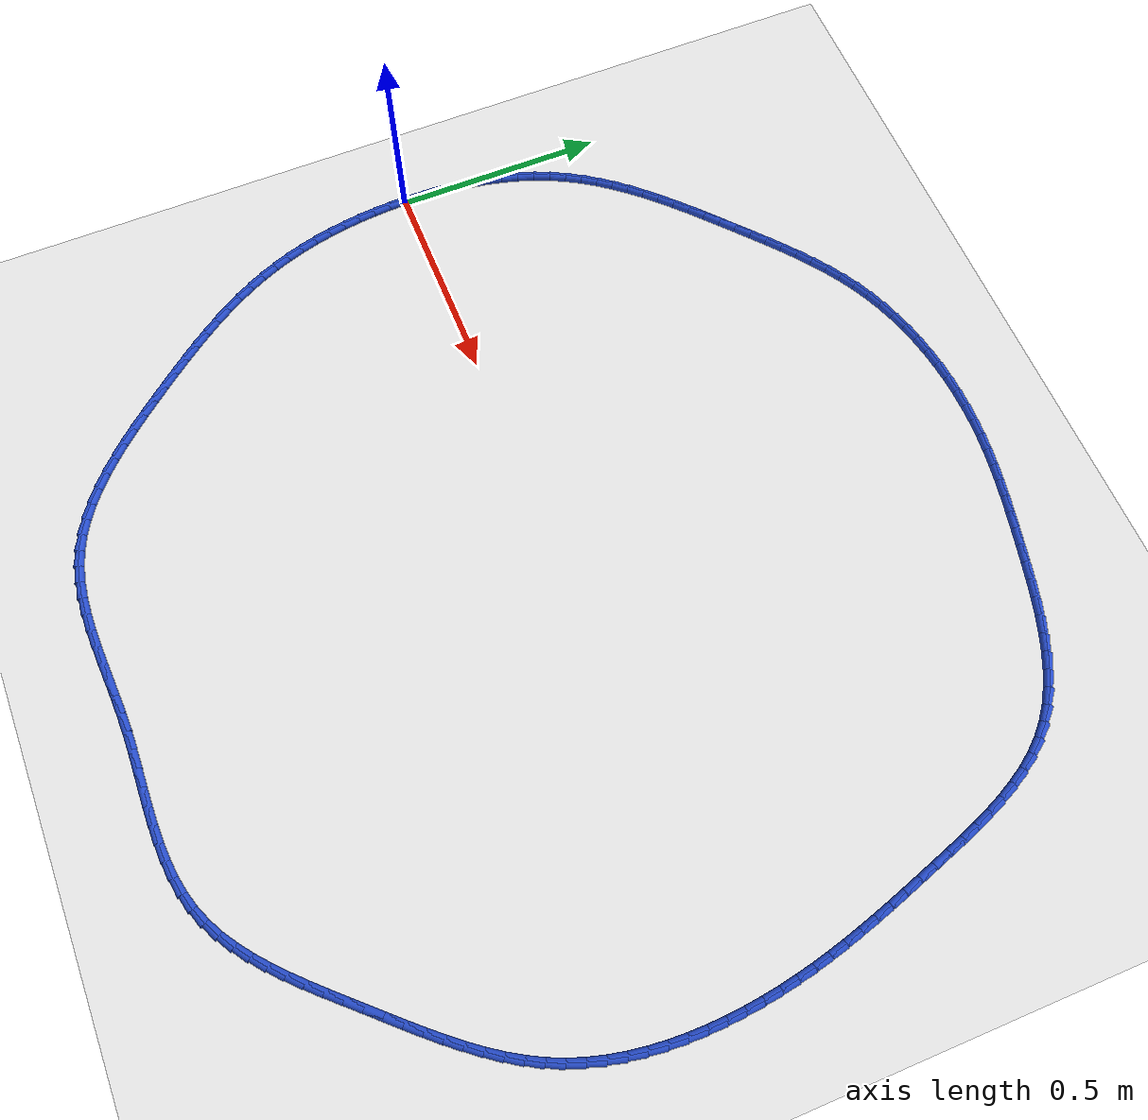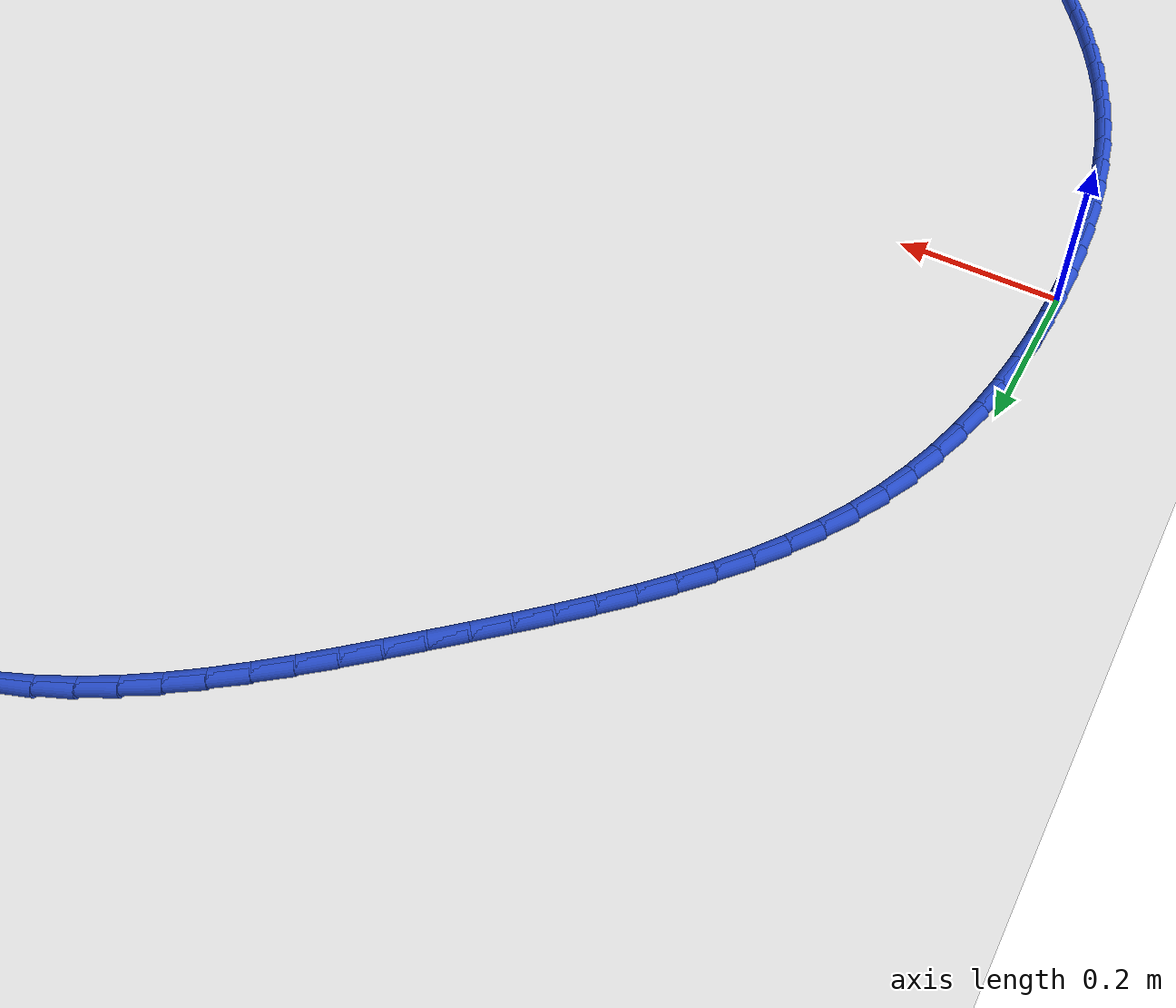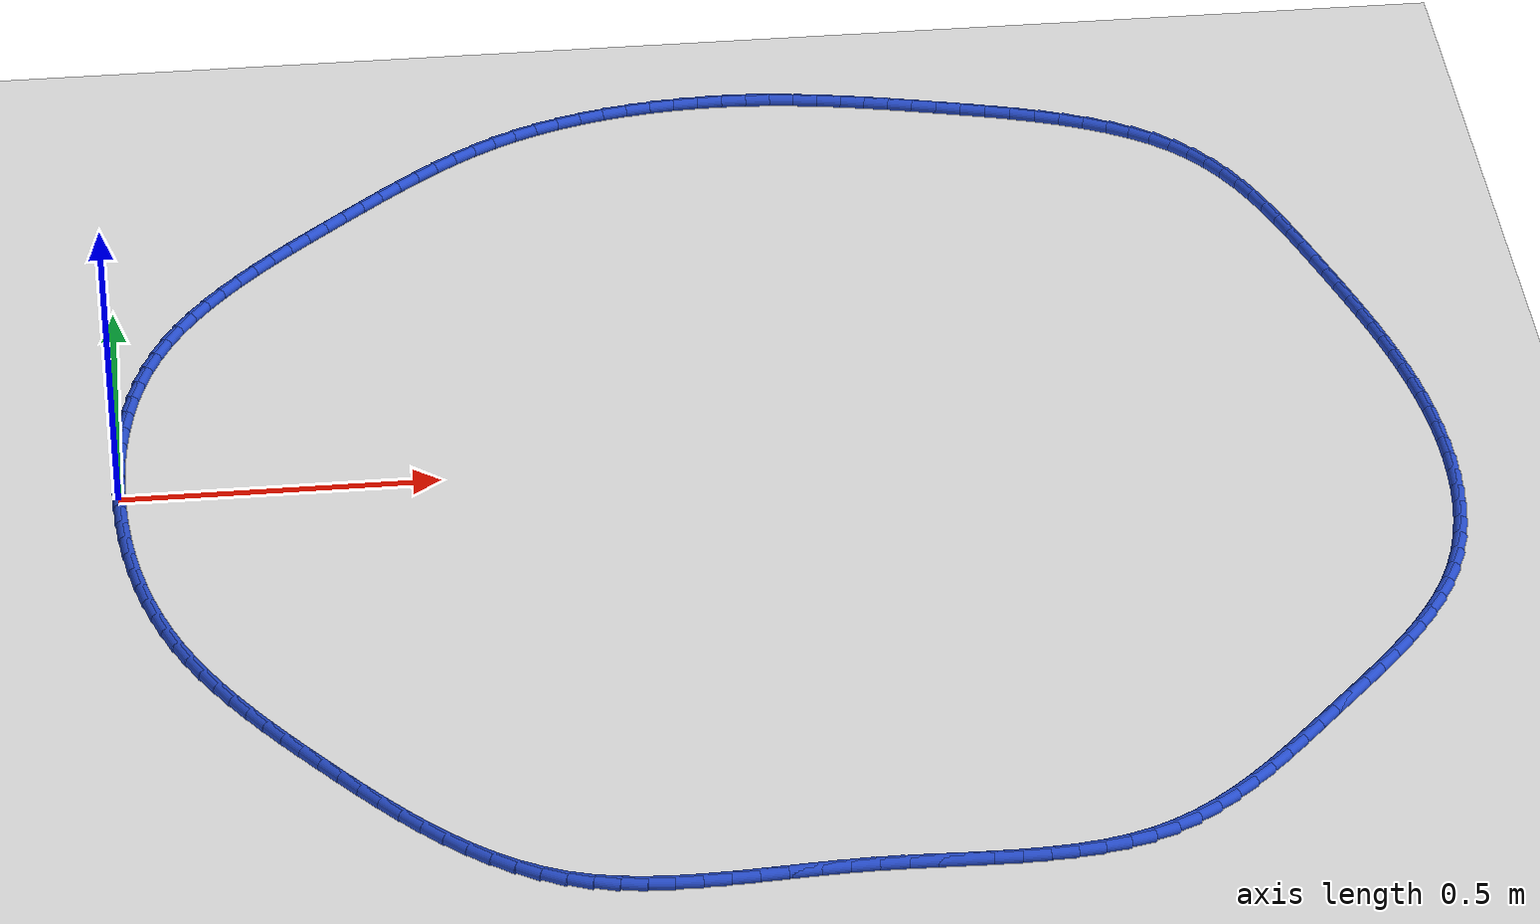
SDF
<sdf version="1.6">
 <world name="default">
  <light name="sun" type="directional">
   <pose>0 0 10 0 -0 0</pose>
   <diffuse>0.8 0.8 0.8 1</diffuse>
   <specular>0.2 0.2 0.2 1</specular>
   <attenuation>
    <range>1000</range>
    <constant>0.9</constant>
    <linear>0.01</linear>
    <quadratic>0.001</quadratic>
   </attenuation>
   <direction>-0.5 0.1 -0.9</direction>
  </light>
  <model name="ground_plane">
   <static>1</static>
   <link name="link">
    <collision name="collision">
     <geometry><plane><normal>0 0 1</normal><size>100 100</size></plane></geometry>
     <surface><friction><ode><mu>100</mu><mu2>50</mu2></ode></friction></surface>
    </collision>
    <visual name="visual">
     <cast_shadows>0</cast_shadows>
     <geometry><plane><normal>0 0 1</normal><size>100 100</size></plane></geometry>
     <material>
      <script><uri>file://media/materials/scripts/gazebo.material</uri><name>Gazebo/WhiteGlow</name></script>
     </material>
    </visual>
   </link>
  </model>
  <gravity>0 0 -9.8</gravity>
  <magnetic_field>6e-06 2.3e-05 -4.2e-05</magnetic_field>
  <atmosphere type="adiabatic"/>
  <physics name="default_physics" default="0" type="ode">
   <max_step_size>0.001</max_step_size>
   <real_time_factor>1</real_time_factor>
   <real_time_update_rate>1000</real_time_update_rate>
  </physics>
  <scene><ambient>0.4 0.4 0.4 1</ambient><background>0.7 0.7 0.7 1</background><shadows>1</shadows></scene>
  <spherical_coordinates>
   <surface_model>EARTH_WGS84</surface_model>
   <latitude_deg>0</latitude_deg>
   <longitude_deg>0</longitude_deg>
   <elevation>0</elevation>
   <heading_deg>0</heading_deg>
  </spherical_coordinates>
  <model name="line">
   <link name="link_0">
    <pose>-7.806255641895632e-18 -4.163336342344337e-17 0.01 0 1.57 1.5649459969162127</pose>
    <collision name="collision">
     <geometry><cylinder><radius>0.01</radius><length>0.08</length></cylinder></geometry>
    </collision>
    <visual name="visual">
     <material>
      <script><name>Gazebo/Blue</name><uri>file://media/materials/scripts/gazebo.material</uri></script>
     </material>
     <geometry><cylinder><radius>0.01</radius><length>0.08</length></cylinder></geometry>
    </visual>
   </link>
   <link name="link_1">
    <pose>0.00024366222345821126 0.0416488383756562 0.01 0 1.57 1.5284976969318906</pose>
    <collision name="collision">
     <geometry><cylinder><radius>0.01</radius><length>0.08</length></cylinder></geometry>
    </collision>
    <visual name="visual">
     <material>
      <script><name>Gazebo/Blue</name><uri>file://media/materials/scripts/gazebo.material</uri></script>
     </material>
     <geometry><cylinder><radius>0.01</radius><length>0.08</length></cylinder></geometry>
    </visual>
   </link>
   <link name="link_2">
    <pose>0.0020040392612818473 0.08324184137865195 0.01 0 1.57 1.489297813799349</pose>
    <collision name="collision">
     <geometry><cylinder><radius>0.01</radius><length>0.08</length></cylinder></geometry>
    </collision>
    <visual name="visual">
     <material>
      <script><name>Gazebo/Blue</name><uri>file://media/materials/scripts/gazebo.material</uri></script>
     </material>
     <geometry><cylinder><radius>0.01</radius><length>0.08</length></cylinder></geometry>
    </visual>
   </link>
   <link name="link_3">
    <pose>0.005384640066235308 0.1246304840163369 0.01 0 1.57 1.4470444961710467</pose>
    <collision name="collision">
     <geometry><cylinder><radius>0.01</radius><length>0.08</length></cylinder></geometry>
    </collision>
    <visual name="visual">
     <material>
      <script><name>Gazebo/Blue</name><uri>file://media/materials/scripts/gazebo.material</uri></script>
     </material>
     <geometry><cylinder><radius>0.01</radius><length>0.08</length></cylinder></geometry>
    </visual>
   </link>
   <link name="link_4">
    <pose>0.01048897359108299 0.1656662412960608 0.01 0 1.57 1.4014295799699183</pose>
    <collision name="collision">
     <geometry><cylinder><radius>0.01</radius><length>0.08</length></cylinder></geometry>
    </collision>
    <visual name="visual">
     <material>
      <script><name>Gazebo/Blue</name><uri>file://media/materials/scripts/gazebo.material</uri></script>
     </material>
     <geometry><cylinder><radius>0.01</radius><length>0.08</length></cylinder></geometry>
    </visual>
   </link>
   <link name="link_5">
    <pose>0.0174205487885893 0.20620058822517334 0.01 0 1.57 1.3521483288717062</pose>
    <collision name="collision">
     <geometry><cylinder><radius>0.01</radius><length>0.08</length></cylinder></geometry>
    </collision>
    <visual name="visual">
     <material>
      <script><name>Gazebo/Blue</name><uri>file://media/materials/scripts/gazebo.material</uri></script>
     </material>
     <geometry><cylinder><radius>0.01</radius><length>0.08</length></cylinder></geometry>
    </visual>
   </link>
   <link name="link_6">
    <pose>0.026282874611518646 0.2460849998110243 0.01 0 1.57 1.2989144465532263</pose>
    <collision name="collision">
     <geometry><cylinder><radius>0.01</radius><length>0.08</length></cylinder></geometry>
    </collision>
    <visual name="visual">
     <material>
      <script><name>Gazebo/Blue</name><uri>file://media/materials/scripts/gazebo.material</uri></script>
     </material>
     <geometry><cylinder><radius>0.01</radius><length>0.08</length></cylinder></geometry>
    </visual>
   </link>
   <link name="link_7">
    <pose>0.037179460012635425 0.2851709510609634 0.01 0 1.57 1.2414814882196221</pose>
    <collision name="collision">
     <geometry><cylinder><radius>0.01</radius><length>0.08</length></cylinder></geometry>
    </collision>
    <visual name="visual">
     <material>
      <script><name>Gazebo/Blue</name><uri>file://media/materials/scripts/gazebo.material</uri></script>
     </material>
     <geometry><cylinder><radius>0.01</radius><length>0.08</length></cylinder></geometry>
    </visual>
   </link>
   <link name="link_8">
    <pose>0.05021381394470403 0.3233099169823404 0.01 0 1.57 1.1796713499881897</pose>
    <collision name="collision">
     <geometry><cylinder><radius>0.01</radius><length>0.08</length></cylinder></geometry>
    </collision>
    <visual name="visual">
     <material>
      <script><name>Gazebo/Blue</name><uri>file://media/materials/scripts/gazebo.material</uri></script>
     </material>
     <geometry><cylinder><radius>0.01</radius><length>0.08</length></cylinder></geometry>
    </visual>
   </link>
   <link name="link_9">
    <pose>0.06548944536048888 0.360353372582505 0.01 0 1.57 1.1135019314614432</pose>
    <collision name="collision">
     <geometry><cylinder><radius>0.01</radius><length>0.08</length></cylinder></geometry>
    </collision>
    <visual name="visual">
     <material>
      <script><name>Gazebo/Blue</name><uri>file://media/materials/scripts/gazebo.material</uri></script>
     </material>
     <geometry><cylinder><radius>0.01</radius><length>0.08</length></cylinder></geometry>
    </visual>
   </link>
   <link name="link_10">
    <pose>0.08310690623043958 0.39615514202409247 0.01 0 1.57 1.0471465379413225</pose>
    <collision name="collision">
     <geometry><cylinder><radius>0.01</radius><length>0.08</length></cylinder></geometry>
    </collision>
    <visual name="visual">
     <material>
      <script><name>Gazebo/Blue</name><uri>file://media/materials/scripts/gazebo.material</uri></script>
     </material>
     <geometry><cylinder><radius>0.01</radius><length>0.08</length></cylinder></geometry>
    </visual>
   </link>
   <link name="link_11">
    <pose>0.10303744204814254 0.43067177615568436 0.01 0 1.57 0.9865613505347274</pose>
    <collision name="collision">
     <geometry><cylinder><radius>0.01</radius><length>0.08</length></cylinder></geometry>
    </collision>
    <visual name="visual">
     <material>
      <script><name>Gazebo/Blue</name><uri>file://media/materials/scripts/gazebo.material</uri></script>
     </material>
     <geometry><cylinder><radius>0.01</radius><length>0.08</length></cylinder></geometry>
    </visual>
   </link>
   <link name="link_12">
    <pose>0.1250755141462379 0.4640002708478141 0.01 0 1.57 0.9324409511440511</pose>
    <collision name="collision">
     <geometry><cylinder><radius>0.01</radius><length>0.08</length></cylinder></geometry>
    </collision>
    <visual name="visual">
     <material>
      <script><name>Gazebo/Blue</name><uri>file://media/materials/scripts/gazebo.material</uri></script>
     </material>
     <geometry><cylinder><radius>0.01</radius><length>0.08</length></cylinder></geometry>
    </visual>
   </link>
   <link name="link_13">
    <pose>0.14900283923948468 0.4962477468494464 0.01 0 1.57 0.8848595708796757</pose>
    <collision name="collision">
     <geometry><cylinder><radius>0.01</radius><length>0.08</length></cylinder></geometry>
    </collision>
    <visual name="visual">
     <material>
      <script><name>Gazebo/Blue</name><uri>file://media/materials/scripts/gazebo.material</uri></script>
     </material>
     <geometry><cylinder><radius>0.01</radius><length>0.08</length></cylinder></geometry>
    </visual>
   </link>
   <link name="link_14">
    <pose>0.17460113404264208 0.5275213249095465 0.01 0 1.57 0.8437368528639989</pose>
    <collision name="collision">
     <geometry><cylinder><radius>0.01</radius><length>0.08</length></cylinder></geometry>
    </collision>
    <visual name="visual">
     <material>
      <script><name>Gazebo/Blue</name><uri>file://media/materials/scripts/gazebo.material</uri></script>
     </material>
     <geometry><cylinder><radius>0.01</radius><length>0.08</length></cylinder></geometry>
    </visual>
   </link>
   <link name="link_15">
    <pose>0.20165211527046892 0.5579281257770786 0.01 0 1.57 0.8088998016578195</pose>
    <collision name="collision">
     <geometry><cylinder><radius>0.01</radius><length>0.08</length></cylinder></geometry>
    </collision>
    <visual name="visual">
     <material>
      <script><name>Gazebo/Blue</name><uri>file://media/materials/scripts/gazebo.material</uri></script>
     </material>
     <geometry><cylinder><radius>0.01</radius><length>0.08</length></cylinder></geometry>
    </visual>
   </link>
   <link name="link_16">
    <pose>0.22993749963772456 0.5875752702010081 0.01 0 1.57 0.7801337874116763</pose>
    <collision name="collision">
     <geometry><cylinder><radius>0.01</radius><length>0.08</length></cylinder></geometry>
    </collision>
    <visual name="visual">
     <material>
      <script><name>Gazebo/Blue</name><uri>file://media/materials/scripts/gazebo.material</uri></script>
     </material>
     <geometry><cylinder><radius>0.01</radius><length>0.08</length></cylinder></geometry>
    </visual>
   </link>
   <link name="link_17">
    <pose>0.25923900385916776 0.6165698789302991 0.01 0 1.57 0.7572213645388868</pose>
    <collision name="collision">
     <geometry><cylinder><radius>0.01</radius><length>0.08</length></cylinder></geometry>
    </collision>
    <visual name="visual">
     <material>
      <script><name>Gazebo/Blue</name><uri>file://media/materials/scripts/gazebo.material</uri></script>
     </material>
     <geometry><cylinder><radius>0.01</radius><length>0.08</length></cylinder></geometry>
    </visual>
   </link>
   <link name="link_18">
    <pose>0.2893383446495577 0.6450190727139168 0.01 0 1.57 0.7399701808898237</pose>
    <collision name="collision">
     <geometry><cylinder><radius>0.01</radius><length>0.08</length></cylinder></geometry>
    </collision>
    <visual name="visual">
     <material>
      <script><name>Gazebo/Blue</name><uri>file://media/materials/scripts/gazebo.material</uri></script>
     </material>
     <geometry><cylinder><radius>0.01</radius><length>0.08</length></cylinder></geometry>
    </visual>
   </link>
   <link name="link_19">
    <pose>0.3200172387236534 0.6730299723008258 0.01 0 1.57 0.7282322431111798</pose>
    <collision name="collision">
     <geometry><cylinder><radius>0.01</radius><length>0.08</length></cylinder></geometry>
    </collision>
    <visual name="visual">
     <material>
      <script><name>Gazebo/Blue</name><uri>file://media/materials/scripts/gazebo.material</uri></script>
     </material>
     <geometry><cylinder><radius>0.01</radius><length>0.08</length></cylinder></geometry>
    </visual>
   </link>
   <link name="link_20">
    <pose>0.3510574027962141 0.7007096984399913 0.01 0 1.57 0.7219168613986632</pose>
    <collision name="collision">
     <geometry><cylinder><radius>0.01</radius><length>0.08</length></cylinder></geometry>
    </collision>
    <visual name="visual">
     <material>
      <script><name>Gazebo/Blue</name><uri>file://media/materials/scripts/gazebo.material</uri></script>
     </material>
     <geometry><cylinder><radius>0.01</radius><length>0.08</length></cylinder></geometry>
    </visual>
   </link>
   <link name="link_21">
    <pose>0.3822405535819986 0.7281653718803776 0.01 0 1.57 0.7192367237158173</pose>
    <collision name="collision">
     <geometry><cylinder><radius>0.01</radius><length>0.08</length></cylinder></geometry>
    </collision>
    <visual name="visual">
     <material>
      <script><name>Gazebo/Blue</name><uri>file://media/materials/scripts/gazebo.material</uri></script>
     </material>
     <geometry><cylinder><radius>0.01</radius><length>0.08</length></cylinder></geometry>
    </visual>
   </link>
   <link name="link_22">
    <pose>0.41340263491358825 0.7554545791969168 0.01 0 1.57 0.7121385850961865</pose>
    <collision name="collision">
     <geometry><cylinder><radius>0.01</radius><length>0.08</length></cylinder></geometry>
    </collision>
    <visual name="visual">
     <material>
      <script><name>Gazebo/Blue</name><uri>file://media/materials/scripts/gazebo.material</uri></script>
     </material>
     <geometry><cylinder><radius>0.01</radius><length>0.08</length></cylinder></geometry>
    </visual>
   </link>
   <link name="link_23">
    <pose>0.44462687032180986 0.7824090274396907 0.01 0 1.57 0.698238150323742</pose>
    <collision name="collision">
     <geometry><cylinder><radius>0.01</radius><length>0.08</length></cylinder></geometry>
    </collision>
    <visual name="visual">
     <material>
      <script><name>Gazebo/Blue</name><uri>file://media/materials/scripts/gazebo.material</uri></script>
     </material>
     <geometry><cylinder><radius>0.01</radius><length>0.08</length></cylinder></geometry>
    </visual>
   </link>
   <link name="link_24">
    <pose>0.4760669299893694 0.8087960736277567 0.01 0 1.57 0.6774064158094336</pose>
    <collision name="collision">
     <geometry><cylinder><radius>0.01</radius><length>0.08</length></cylinder></geometry>
    </collision>
    <visual name="visual">
     <material>
      <script><name>Gazebo/Blue</name><uri>file://media/materials/scripts/gazebo.material</uri></script>
     </material>
     <geometry><cylinder><radius>0.01</radius><length>0.08</length></cylinder></geometry>
    </visual>
   </link>
   <link name="link_25">
    <pose>0.5078764892489078 0.8343830700759255 0.01 0 1.57 0.6495061133031699</pose>
    <collision name="collision">
     <geometry><cylinder><radius>0.01</radius><length>0.08</length></cylinder></geometry>
    </collision>
    <visual name="visual">
     <material>
      <script><name>Gazebo/Blue</name><uri>file://media/materials/scripts/gazebo.material</uri></script>
     </material>
     <geometry><cylinder><radius>0.01</radius><length>0.08</length></cylinder></geometry>
    </visual>
   </link>
   <link name="link_26">
    <pose>0.5402092234330662 0.8589373690990075 0.01 0 1.57 0.6144217082321504</pose>
    <collision name="collision">
     <geometry><cylinder><radius>0.01</radius><length>0.08</length></cylinder></geometry>
    </collision>
    <visual name="visual">
     <material>
      <script><name>Gazebo/Blue</name><uri>file://media/materials/scripts/gazebo.material</uri></script>
     </material>
     <geometry><cylinder><radius>0.01</radius><length>0.08</length></cylinder></geometry>
    </visual>
   </link>
   <link name="link_27">
    <pose>0.5732188078744854 0.882226323011813 0.01 0 1.57 0.5721024901566106</pose>
    <collision name="collision">
     <geometry><cylinder><radius>0.01</radius><length>0.08</length></cylinder></geometry>
    </collision>
    <visual name="visual">
     <material>
      <script><name>Gazebo/Blue</name><uri>file://media/materials/scripts/gazebo.material</uri></script>
     </material>
     <geometry><cylinder><radius>0.01</radius><length>0.08</length></cylinder></geometry>
    </visual>
   </link>
   <link name="link_28">
    <pose>0.607058917905806 0.9040172841291522 0.01 0 1.57 0.522618201694443</pose>
    <collision name="collision">
     <geometry><cylinder><radius>0.01</radius><length>0.08</length></cylinder></geometry>
    </collision>
    <visual name="visual">
     <material>
      <script><name>Gazebo/Blue</name><uri>file://media/materials/scripts/gazebo.material</uri></script>
     </material>
     <geometry><cylinder><radius>0.01</radius><length>0.08</length></cylinder></geometry>
    </visual>
   </link>
   <link name="link_29">
    <pose>0.6418832288596692 0.9240776047658356 0.01 0 1.57 0.46623008231712626</pose>
    <collision name="collision">
     <geometry><cylinder><radius>0.01</radius><length>0.08</length></cylinder></geometry>
    </collision>
    <visual name="visual">
     <material>
      <script><name>Gazebo/Blue</name><uri>file://media/materials/scripts/gazebo.material</uri></script>
     </material>
     <geometry><cylinder><radius>0.01</radius><length>0.08</length></cylinder></geometry>
    </visual>
   </link>
   <link name="link_30">
    <pose>0.6778451977279444 0.9421748280815396 0.01 0 1.57 0.4058939648808866</pose>
    <collision name="collision">
     <geometry><cylinder><radius>0.01</radius><length>0.08</length></cylinder></geometry>
    </collision>
    <visual name="visual">
     <material>
      <script><name>Gazebo/Blue</name><uri>file://media/materials/scripts/gazebo.material</uri></script>
     </material>
     <geometry><cylinder><radius>0.01</radius><length>0.08</length></cylinder></geometry>
    </visual>
   </link>
   <link name="link_31">
    <pose>0.7150153343546467 0.9581489987539107 0.01 0 1.57 0.3479993224994982</pose>
    <collision name="collision">
     <geometry><cylinder><radius>0.01</radius><length>0.08</length></cylinder></geometry>
    </collision>
    <visual name="visual">
     <material>
      <script><name>Gazebo/Blue</name><uri>file://media/materials/scripts/gazebo.material</uri></script>
     </material>
     <geometry><cylinder><radius>0.01</radius><length>0.08</length></cylinder></geometry>
    </visual>
   </link>
   <link name="link_32">
    <pose>0.7532566505563638 0.9720215290223849 0.01 0 1.57 0.2932633993868242</pose>
    <collision name="collision">
     <geometry><cylinder><radius>0.01</radius><length>0.08</length></cylinder></geometry>
    </collision>
    <visual name="visual">
     <material>
      <script><name>Gazebo/Blue</name><uri>file://media/materials/scripts/gazebo.material</uri></script>
     </material>
     <geometry><cylinder><radius>0.01</radius><length>0.08</length></cylinder></geometry>
    </visual>
   </link>
   <link name="link_33">
    <pose>0.7924002404395777 0.9838417294025015 0.01 0 1.57 0.24138657109106942</pose>
    <collision name="collision">
     <geometry><cylinder><radius>0.01</radius><length>0.08</length></cylinder></geometry>
    </collision>
    <visual name="visual">
     <material>
      <script><name>Gazebo/Blue</name><uri>file://media/materials/scripts/gazebo.material</uri></script>
     </material>
     <geometry><cylinder><radius>0.01</radius><length>0.08</length></cylinder></geometry>
    </visual>
   </link>
   <link name="link_34">
    <pose>0.832277198110771 0.9936589104097997 0.01 0 1.57 0.19204474803485463</pose>
    <collision name="collision">
     <geometry><cylinder><radius>0.01</radius><length>0.08</length></cylinder></geometry>
    </collision>
    <visual name="visual">
     <material>
      <script><name>Gazebo/Blue</name><uri>file://media/materials/scripts/gazebo.material</uri></script>
     </material>
     <geometry><cylinder><radius>0.01</radius><length>0.08</length></cylinder></geometry>
    </visual>
   </link>
   <link name="link_35">
    <pose>0.8727186176764252 1.001522382559818 0.01 0 1.57 0.1449007718088609</pose>
    <collision name="collision">
     <geometry><cylinder><radius>0.01</radius><length>0.08</length></cylinder></geometry>
    </collision>
    <visual name="visual">
     <material>
      <script><name>Gazebo/Blue</name><uri>file://media/materials/scripts/gazebo.material</uri></script>
     </material>
     <geometry><cylinder><radius>0.01</radius><length>0.08</length></cylinder></geometry>
    </visual>
   </link>
   <link name="link_36">
    <pose>0.9135555932430234 1.007481456368096 0.01 0 1.57 0.09961134950780197</pose>
    <collision name="collision">
     <geometry><cylinder><radius>0.01</radius><length>0.08</length></cylinder></geometry>
    </collision>
    <visual name="visual">
     <material>
      <script><name>Gazebo/Blue</name><uri>file://media/materials/scripts/gazebo.material</uri></script>
     </material>
     <geometry><cylinder><radius>0.01</radius><length>0.08</length></cylinder></geometry>
    </visual>
   </link>
   <link name="link_37">
    <pose>0.9546192189170475 1.0115854423501731 0.01 0 1.57 0.05583034615350159</pose>
    <collision name="collision">
     <geometry><cylinder><radius>0.01</radius><length>0.08</length></cylinder></geometry>
    </collision>
    <visual name="visual">
     <material>
      <script><name>Gazebo/Blue</name><uri>file://media/materials/scripts/gazebo.material</uri></script>
     </material>
     <geometry><cylinder><radius>0.01</radius><length>0.08</length></cylinder></geometry>
    </visual>
   </link>
   <link name="link_38">
    <pose>0.9957405888049795 1.0138836510215876 0.01 0 1.57 0.013209159171409149</pose>
    <collision name="collision">
     <geometry><cylinder><radius>0.01</radius><length>0.08</length></cylinder></geometry>
    </collision>
    <visual name="visual">
     <material>
      <script><name>Gazebo/Blue</name><uri>file://media/materials/scripts/gazebo.material</uri></script>
     </material>
     <geometry><cylinder><radius>0.01</radius><length>0.08</length></cylinder></geometry>
    </visual>
   </link>
   <link name="link_39">
    <pose>1.0367507970133014 1.0144253928978786 0.01 0 1.57 -0.028605266189398515</pose>
    <collision name="collision">
     <geometry><cylinder><radius>0.01</radius><length>0.08</length></cylinder></geometry>
    </collision>
    <visual name="visual">
     <material>
      <script><name>Gazebo/Blue</name><uri>file://media/materials/scripts/gazebo.material</uri></script>
     </material>
     <geometry><cylinder><radius>0.01</radius><length>0.08</length></cylinder></geometry>
    </visual>
   </link>
   <link name="link_40">
    <pose>1.0774809376484957 1.0132599784945855 0.01 0 1.57 -0.06942494627487604</pose>
    <collision name="collision">
     <geometry><cylinder><radius>0.01</radius><length>0.08</length></cylinder></geometry>
    </collision>
    <visual name="visual">
     <material>
      <script><name>Gazebo/Blue</name><uri>file://media/materials/scripts/gazebo.material</uri></script>
     </material>
     <geometry><cylinder><radius>0.01</radius><length>0.08</length></cylinder></geometry>
    </visual>
   </link>
   <link name="link_41">
    <pose>1.117806039749113 1.0104559039516745 0.01 0 1.57 -0.10687129788580829</pose>
    <collision name="collision">
     <geometry><cylinder><radius>0.01</radius><length>0.08</length></cylinder></geometry>
    </collision>
    <visual name="visual">
     <material>
      <script><name>Gazebo/Blue</name><uri>file://media/materials/scripts/gazebo.material</uri></script>
     </material>
     <geometry><cylinder><radius>0.01</radius><length>0.08</length></cylinder></geometry>
    </visual>
   </link>
   <link name="link_42">
    <pose>1.1577941958818514 1.0061659729103958 0.01 0 1.57 -0.13987777914664257</pose>
    <collision name="collision">
     <geometry><cylinder><radius>0.01</radius><length>0.08</length></cylinder></geometry>
    </collision>
    <visual name="visual">
     <material>
      <script><name>Gazebo/Blue</name><uri>file://media/materials/scripts/gazebo.material</uri></script>
     </material>
     <geometry><cylinder><radius>0.01</radius><length>0.08</length></cylinder></geometry>
    </visual>
   </link>
   <link name="link_43">
    <pose>1.1975665140257667 1.0005661399250065 0.01 0 1.57 -0.16811064082272698</pose>
    <collision name="collision">
     <geometry><cylinder><radius>0.01</radius><length>0.08</length></cylinder></geometry>
    </collision>
    <visual name="visual">
     <material>
      <script><name>Gazebo/Blue</name><uri>file://media/materials/scripts/gazebo.material</uri></script>
     </material>
     <geometry><cylinder><radius>0.01</radius><length>0.08</length></cylinder></geometry>
    </visual>
   </link>
   <link name="link_44">
    <pose>1.2372441036450272 0.9938323601982882 0.01 0 1.57 -0.19135759226672464</pose>
    <collision name="collision">
     <geometry><cylinder><radius>0.01</radius><length>0.08</length></cylinder></geometry>
    </collision>
    <visual name="visual">
     <material>
      <script><name>Gazebo/Blue</name><uri>file://media/materials/scripts/gazebo.material</uri></script>
     </material>
     <geometry><cylinder><radius>0.01</radius><length>0.08</length></cylinder></geometry>
    </visual>
   </link>
   <link name="link_45">
    <pose>1.2769480742038002 0.9861405889330218 0.01 0 1.57 -0.20951436941970664</pose>
    <collision name="collision">
     <geometry><cylinder><radius>0.01</radius><length>0.08</length></cylinder></geometry>
    </collision>
    <visual name="visual">
     <material>
      <script><name>Gazebo/Blue</name><uri>file://media/materials/scripts/gazebo.material</uri></script>
     </material>
     <geometry><cylinder><radius>0.01</radius><length>0.08</length></cylinder></geometry>
    </visual>
   </link>
   <link name="link_46">
    <pose>1.3167995351662545 0.9776667813319883 0.01 0 1.57 -0.22256850336323453</pose>
    <collision name="collision">
     <geometry><cylinder><radius>0.01</radius><length>0.08</length></cylinder></geometry>
    </collision>
    <visual name="visual">
     <material>
      <script><name>Gazebo/Blue</name><uri>file://media/materials/scripts/gazebo.material</uri></script>
     </material>
     <geometry><cylinder><radius>0.01</radius><length>0.08</length></cylinder></geometry>
    </visual>
   </link>
   <link name="link_47">
    <pose>1.3569195959965565 0.9685868925979682 0.01 0 1.57 -0.23058313491844468</pose>
    <collision name="collision">
     <geometry><cylinder><radius>0.01</radius><length>0.08</length></cylinder></geometry>
    </collision>
    <visual name="visual">
     <material>
      <script><name>Gazebo/Blue</name><uri>file://media/materials/scripts/gazebo.material</uri></script>
     </material>
     <geometry><cylinder><radius>0.01</radius><length>0.08</length></cylinder></geometry>
    </visual>
   </link>
   <link name="link_48">
    <pose>1.397429365941651 0.9590768777201986 0.01 0 1.57 -0.23593071247263447</pose>
    <collision name="collision">
     <geometry><cylinder><radius>0.01</radius><length>0.08</length></cylinder></geometry>
    </collision>
    <visual name="visual">
     <material>
      <script><name>Gazebo/Blue</name><uri>file://media/materials/scripts/gazebo.material</uri></script>
     </material>
     <geometry><cylinder><radius>0.01</radius><length>0.08</length></cylinder></geometry>
    </visual>
   </link>
   <link name="link_49">
    <pose>1.438370269826245 0.9492343574030682 0.01 0 1.57 -0.24728312318332435</pose>
    <collision name="collision">
     <geometry><cylinder><radius>0.01</radius><length>0.08</length></cylinder></geometry>
    </collision>
    <visual name="visual">
     <material>
      <script><name>Gazebo/Blue</name><uri>file://media/materials/scripts/gazebo.material</uri></script>
     </material>
     <geometry><cylinder><radius>0.01</radius><length>0.08</length></cylinder></geometry>
    </visual>
   </link>
   <link name="link_50">
    <pose>1.4794782547721101 0.9388566505262729 0.01 0 1.57 -0.2667672953551547</pose>
    <collision name="collision">
     <geometry><cylinder><radius>0.01</radius><length>0.08</length></cylinder></geometry>
    </collision>
    <visual name="visual">
     <material>
      <script><name>Gazebo/Blue</name><uri>file://media/materials/scripts/gazebo.material</uri></script>
     </material>
     <geometry><cylinder><radius>0.01</radius><length>0.08</length></cylinder></geometry>
    </visual>
   </link>
   <link name="link_51">
    <pose>1.5204160766709118 0.9276691248590326 0.01 0 1.57 -0.29469518178689097</pose>
    <collision name="collision">
     <geometry><cylinder><radius>0.01</radius><length>0.08</length></cylinder></geometry>
    </collision>
    <visual name="visual">
     <material>
      <script><name>Gazebo/Blue</name><uri>file://media/materials/scripts/gazebo.material</uri></script>
     </material>
     <geometry><cylinder><radius>0.01</radius><length>0.08</length></cylinder></geometry>
    </visual>
   </link>
   <link name="link_52">
    <pose>1.5608464914143148 0.9153971481705673 0.01 0 1.57 -0.33162584808636714</pose>
    <collision name="collision">
     <geometry><cylinder><radius>0.01</radius><length>0.08</length></cylinder></geometry>
    </collision>
    <visual name="visual">
     <material>
      <script><name>Gazebo/Blue</name><uri>file://media/materials/scripts/gazebo.material</uri></script>
     </material>
     <geometry><cylinder><radius>0.01</radius><length>0.08</length></cylinder></geometry>
    </visual>
   </link>
   <link name="link_53">
    <pose>1.600432254893986 0.9017660882300967 0.01 0 1.57 -0.37833221064710937</pose>
    <collision name="collision">
     <geometry><cylinder><radius>0.01</radius><length>0.08</length></cylinder></geometry>
    </collision>
    <visual name="visual">
     <material>
      <script><name>Gazebo/Blue</name><uri>file://media/materials/scripts/gazebo.material</uri></script>
     </material>
     <geometry><cylinder><radius>0.01</radius><length>0.08</length></cylinder></geometry>
    </visual>
   </link>
   <link name="link_54">
    <pose>1.6388361230015893 0.8865013128068412 0.01 0 1.57 -0.435741831799265</pose>
    <collision name="collision">
     <geometry><cylinder><radius>0.01</radius><length>0.08</length></cylinder></geometry>
    </collision>
    <visual name="visual">
     <material>
      <script><name>Gazebo/Blue</name><uri>file://media/materials/scripts/gazebo.material</uri></script>
     </material>
     <geometry><cylinder><radius>0.01</radius><length>0.08</length></cylinder></geometry>
    </visual>
   </link>
   <link name="link_55">
    <pose>1.6757208516287918 0.8693281896700208 0.01 0 1.57 -0.504824924632468</pose>
    <collision name="collision">
     <geometry><cylinder><radius>0.01</radius><length>0.08</length></cylinder></geometry>
    </collision>
    <visual name="visual">
     <material>
      <script><name>Gazebo/Blue</name><uri>file://media/materials/scripts/gazebo.material</uri></script>
     </material>
     <geometry><cylinder><radius>0.01</radius><length>0.08</length></cylinder></geometry>
    </visual>
   </link>
   <link name="link_56">
    <pose>1.7107491966672586 0.8499720865888549 0.01 0 1.57 -0.586396424867699</pose>
    <collision name="collision">
     <geometry><cylinder><radius>0.01</radius><length>0.08</length></cylinder></geometry>
    </collision>
    <visual name="visual">
     <material>
      <script><name>Gazebo/Blue</name><uri>file://media/materials/scripts/gazebo.material</uri></script>
     </material>
     <geometry><cylinder><radius>0.01</radius><length>0.08</length></cylinder></geometry>
    </visual>
   </link>
   <link name="link_57">
    <pose>1.743583914008655 0.8281583713325641 0.01 0 1.57 -0.6808057359868638</pose>
    <collision name="collision">
     <geometry><cylinder><radius>0.01</radius><length>0.08</length></cylinder></geometry>
    </collision>
    <visual name="visual">
     <material>
      <script><name>Gazebo/Blue</name><uri>file://media/materials/scripts/gazebo.material</uri></script>
     </material>
     <geometry><cylinder><radius>0.01</radius><length>0.08</length></cylinder></geometry>
    </visual>
   </link>
   <link name="link_58">
    <pose>1.773887759544648 0.8036124116703681 0.01 0 1.57 -0.7867190012757334</pose>
    <collision name="collision">
     <geometry><cylinder><radius>0.01</radius><length>0.08</length></cylinder></geometry>
    </collision>
    <visual name="visual">
     <material>
      <script><name>Gazebo/Blue</name><uri>file://media/materials/scripts/gazebo.material</uri></script>
     </material>
     <geometry><cylinder><radius>0.01</radius><length>0.08</length></cylinder></geometry>
    </visual>
   </link>
   <link name="link_59">
    <pose>1.8013454860646658 0.7760820547646701 0.01 0 1.57 -0.8899946766511091</pose>
    <collision name="collision">
     <geometry><cylinder><radius>0.01</radius><length>0.08</length></cylinder></geometry>
    </collision>
    <visual name="visual">
     <material>
      <script><name>Gazebo/Blue</name><uri>file://media/materials/scripts/gazebo.material</uri></script>
     </material>
     <geometry><cylinder><radius>0.01</radius><length>0.08</length></cylinder></geometry>
    </visual>
   </link>
   <link name="link_60">
    <pose>1.825983505169716 0.7456643007739819 0.01 0 1.57 -0.979455108823791</pose>
    <collision name="collision">
     <geometry><cylinder><radius>0.01</radius><length>0.08</length></cylinder></geometry>
    </collision>
    <visual name="visual">
     <material>
      <script><name>Gazebo/Blue</name><uri>file://media/materials/scripts/gazebo.material</uri></script>
     </material>
     <geometry><cylinder><radius>0.01</radius><length>0.08</length></cylinder></geometry>
    </visual>
   </link>
   <link name="link_61">
    <pose>1.8480977922195192 0.7127316264164983 0.01 0 1.57 -1.054768374926705</pose>
    <collision name="collision">
     <geometry><cylinder><radius>0.01</radius><length>0.08</length></cylinder></geometry>
    </collision>
    <visual name="visual">
     <material>
      <script><name>Gazebo/Blue</name><uri>file://media/materials/scripts/gazebo.material</uri></script>
     </material>
     <geometry><cylinder><radius>0.01</radius><length>0.08</length></cylinder></geometry>
    </visual>
   </link>
   <link name="link_62">
    <pose>1.8679916460829438 0.6776639925585599 0.01 0 1.57 -1.1166351672617465</pose>
    <collision name="collision">
     <geometry><cylinder><radius>0.01</radius><length>0.08</length></cylinder></geometry>
    </collision>
    <visual name="visual">
     <material>
      <script><name>Gazebo/Blue</name><uri>file://media/materials/scripts/gazebo.material</uri></script>
     </material>
     <geometry><cylinder><radius>0.01</radius><length>0.08</length></cylinder></geometry>
    </visual>
   </link>
   <link name="link_63">
    <pose>1.88596836562886 0.6408413600665069 0.01 0 1.57 -1.1660714495590405</pose>
    <collision name="collision">
     <geometry><cylinder><radius>0.01</radius><length>0.08</length></cylinder></geometry>
    </collision>
    <visual name="visual">
     <material>
      <script><name>Gazebo/Blue</name><uri>file://media/materials/scripts/gazebo.material</uri></script>
     </material>
     <geometry><cylinder><radius>0.01</radius><length>0.08</length></cylinder></geometry>
    </visual>
   </link>
   <link name="link_64">
    <pose>1.9023312497261353 0.6026436898066801 0.01 0 1.57 -1.2041068189361204</pose>
    <collision name="collision">
     <geometry><cylinder><radius>0.01</radius><length>0.08</length></cylinder></geometry>
    </collision>
    <visual name="visual">
     <material>
      <script><name>Gazebo/Blue</name><uri>file://media/materials/scripts/gazebo.material</uri></script>
     </material>
     <geometry><cylinder><radius>0.01</radius><length>0.08</length></cylinder></geometry>
    </visual>
   </link>
   <link name="link_65">
    <pose>1.9173835972436395 0.5634509426454196 0.01 0 1.57 -1.2316092471743287</pose>
    <collision name="collision">
     <geometry><cylinder><radius>0.01</radius><length>0.08</length></cylinder></geometry>
    </collision>
    <visual name="visual">
     <material>
      <script><name>Gazebo/Blue</name><uri>file://media/materials/scripts/gazebo.material</uri></script>
     </material>
     <geometry><cylinder><radius>0.01</radius><length>0.08</length></cylinder></geometry>
    </visual>
   </link>
   <link name="link_66">
    <pose>1.9314287070502423 0.5236430794490659 0.01 0 1.57 -1.2491919133903944</pose>
    <collision name="collision">
     <geometry><cylinder><radius>0.01</radius><length>0.08</length></cylinder></geometry>
    </collision>
    <visual name="visual">
     <material>
      <script><name>Gazebo/Blue</name><uri>file://media/materials/scripts/gazebo.material</uri></script>
     </material>
     <geometry><cylinder><radius>0.01</radius><length>0.08</length></cylinder></geometry>
    </visual>
   </link>
   <link name="link_67">
    <pose>1.9447698780148122 0.4836000610839598 0.01 0 1.57 -1.257188649435996</pose>
    <collision name="collision">
     <geometry><cylinder><radius>0.01</radius><length>0.08</length></cylinder></geometry>
    </collision>
    <visual name="visual">
     <material>
      <script><name>Gazebo/Blue</name><uri>file://media/materials/scripts/gazebo.material</uri></script>
     </material>
     <geometry><cylinder><radius>0.01</radius><length>0.08</length></cylinder></geometry>
    </visual>
   </link>
   <link name="link_68">
    <pose>1.957709583214773 0.44370087262716457 0.01 0 1.57 -1.2594267739394696</pose>
    <collision name="collision">
     <geometry><cylinder><radius>0.01</radius><length>0.08</length></cylinder></geometry>
    </collision>
    <visual name="visual">
     <material>
      <script><name>Gazebo/Blue</name><uri>file://media/materials/scripts/gazebo.material</uri></script>
     </material>
     <geometry><cylinder><radius>0.01</radius><length>0.08</length></cylinder></geometry>
    </visual>
   </link>
   <link name="link_69">
    <pose>1.9704286629947136 0.4041807728952091 0.01 0 1.57 -1.2637239103937679</pose>
    <collision name="collision">
     <geometry><cylinder><radius>0.01</radius><length>0.08</length></cylinder></geometry>
    </collision>
    <visual name="visual">
     <material>
      <script><name>Gazebo/Blue</name><uri>file://media/materials/scripts/gazebo.material</uri></script>
     </material>
     <geometry><cylinder><radius>0.01</radius><length>0.08</length></cylinder></geometry>
    </visual>
   </link>
   <link name="link_70">
    <pose>1.9828590440624827 0.3649808940713424 0.01 0 1.57 -1.271102456970719</pose>
    <collision name="collision">
     <geometry><cylinder><radius>0.01</radius><length>0.08</length></cylinder></geometry>
    </collision>
    <visual name="visual">
     <material>
      <script><name>Gazebo/Blue</name><uri>file://media/materials/scripts/gazebo.material</uri></script>
     </material>
     <geometry><cylinder><radius>0.01</radius><length>0.08</length></cylinder></geometry>
    </visual>
   </link>
   <link name="link_71">
    <pose>1.9949022008894843 0.3260063847185581 0.01 0 1.57 -1.2816034752895846</pose>
    <collision name="collision">
     <geometry><cylinder><radius>0.01</radius><length>0.08</length></cylinder></geometry>
    </collision>
    <visual name="visual">
     <material>
      <script><name>Gazebo/Blue</name><uri>file://media/materials/scripts/gazebo.material</uri></script>
     </material>
     <geometry><cylinder><radius>0.01</radius><length>0.08</length></cylinder></geometry>
    </visual>
   </link>
   <link name="link_72">
    <pose>2.006459607947122 0.2871623933998507 0.01 0 1.57 -1.295237514780174</pose>
    <collision name="collision">
     <geometry><cylinder><radius>0.01</radius><length>0.08</length></cylinder></geometry>
    </collision>
    <visual name="visual">
     <material>
      <script><name>Gazebo/Blue</name><uri>file://media/materials/scripts/gazebo.material</uri></script>
     </material>
     <geometry><cylinder><radius>0.01</radius><length>0.08</length></cylinder></geometry>
    </visual>
   </link>
   <link name="link_73">
    <pose>2.0174327397068 0.24835406867821344 0.01 0 1.57 -1.3119804130518693</pose>
    <collision name="collision">
     <geometry><cylinder><radius>0.01</radius><length>0.08</length></cylinder></geometry>
    </collision>
    <visual name="visual">
     <material>
      <script><name>Gazebo/Blue</name><uri>file://media/materials/scripts/gazebo.material</uri></script>
     </material>
     <geometry><cylinder><radius>0.01</radius><length>0.08</length></cylinder></geometry>
    </visual>
   </link>
   <link name="link_74">
    <pose>2.027723070639923 0.20948655911664096 0.01 0 1.57 -1.331769019522971</pose>
    <collision name="collision">
     <geometry><cylinder><radius>0.01</radius><length>0.08</length></cylinder></geometry>
    </collision>
    <visual name="visual">
     <material>
      <script><name>Gazebo/Blue</name><uri>file://media/materials/scripts/gazebo.material</uri></script>
     </material>
     <geometry><cylinder><radius>0.01</radius><length>0.08</length></cylinder></geometry>
    </visual>
   </link>
   <link name="link_75">
    <pose>2.037232075217896 0.17046501327812685 0.01 0 1.57 -1.3544972478748307</pose>
    <collision name="collision">
     <geometry><cylinder><radius>0.01</radius><length>0.08</length></cylinder></geometry>
    </collision>
    <visual name="visual">
     <material>
      <script><name>Gazebo/Blue</name><uri>file://media/materials/scripts/gazebo.material</uri></script>
     </material>
     <geometry><cylinder><radius>0.01</radius><length>0.08</length></cylinder></geometry>
    </visual>
   </link>
   <link name="link_76">
    <pose>2.0458612279121207 0.13119457972566445 0.01 0 1.57 -1.380012985655619</pose>
    <collision name="collision">
     <geometry><cylinder><radius>0.01</radius><length>0.08</length></cylinder></geometry>
    </collision>
    <visual name="visual">
     <material>
      <script><name>Gazebo/Blue</name><uri>file://media/materials/scripts/gazebo.material</uri></script>
     </material>
     <geometry><cylinder><radius>0.01</radius><length>0.08</length></cylinder></geometry>
    </visual>
   </link>
   <link name="link_77">
    <pose>2.0535120031940033 0.09158040702224854 0.01 0 1.57 -1.408116469061944</pose>
    <collision name="collision">
     <geometry><cylinder><radius>0.01</radius><length>0.08</length></cylinder></geometry>
    </collision>
    <visual name="visual">
     <material>
      <script><name>Gazebo/Blue</name><uri>file://media/materials/scripts/gazebo.material</uri></script>
     </material>
     <geometry><cylinder><radius>0.01</radius><length>0.08</length></cylinder></geometry>
    </visual>
   </link>
   <link name="link_78">
    <pose>2.0600858755349476 0.051527643730872284 0.01 0 1.57 -1.4385604136900199</pose>
    <collision name="collision">
     <geometry><cylinder><radius>0.01</radius><length>0.08</length></cylinder></geometry>
    </collision>
    <visual name="visual">
     <material>
      <script><name>Gazebo/Blue</name><uri>file://media/materials/scripts/gazebo.material</uri></script>
     </material>
     <geometry><cylinder><radius>0.01</radius><length>0.08</length></cylinder></geometry>
    </visual>
   </link>
   <link name="link_79">
    <pose>2.065484200657087 0.010942430454969728 0.01 0 1.57 -1.4711004929491247</pose>
    <collision name="collision">
     <geometry><cylinder><radius>0.01</radius><length>0.08</length></cylinder></geometry>
    </collision>
    <visual name="visual">
     <material>
      <script><name>Gazebo/Blue</name><uri>file://media/materials/scripts/gazebo.material</uri></script>
     </material>
     <geometry><cylinder><radius>0.01</radius><length>0.08</length></cylinder></geometry>
    </visual>
   </link>
   <link name="link_80">
    <pose>2.069597078895138 -0.030175063840003086 0.01 0 1.57 -1.5058635354501921</pose>
    <collision name="collision">
     <geometry><cylinder><radius>0.01</radius><length>0.08</length></cylinder></geometry>
    </collision>
    <visual name="visual">
     <material>
      <script><name>Gazebo/Blue</name><uri>file://media/materials/scripts/gazebo.material</uri></script>
     </material>
     <geometry><cylinder><radius>0.01</radius><length>0.08</length></cylinder></geometry>
    </visual>
   </link>
   <link name="link_81">
    <pose>2.0722942525323442 -0.07165459747907219 0.01 0 1.57 -1.5432169029681508</pose>
    <collision name="collision">
     <geometry><cylinder><radius>0.01</radius><length>0.08</length></cylinder></geometry>
    </collision>
    <visual name="visual">
     <material>
      <script><name>Gazebo/Blue</name><uri>file://media/materials/scripts/gazebo.material</uri></script>
     </material>
     <geometry><cylinder><radius>0.01</radius><length>0.08</length></cylinder></geometry>
    </visual>
   </link>
   <link name="link_82">
    <pose>2.073443321619876 -0.11330803241770135 0.01 0 1.57 1.5580341560146838</pose>
    <collision name="collision">
     <geometry><cylinder><radius>0.01</radius><length>0.08</length></cylinder></geometry>
    </collision>
    <visual name="visual">
     <material>
      <script><name>Gazebo/Blue</name><uri>file://media/materials/scripts/gazebo.material</uri></script>
     </material>
     <geometry><cylinder><radius>0.01</radius><length>0.08</length></cylinder></geometry>
    </visual>
   </link>
   <link name="link_83">
    <pose>2.072911886208904 -0.15494723061135213 0.01 0 1.57 1.5142803309099493</pose>
    <collision name="collision">
     <geometry><cylinder><radius>0.01</radius><length>0.08</length></cylinder></geometry>
    </collision>
    <visual name="visual">
     <material>
      <script><name>Gazebo/Blue</name><uri>file://media/materials/scripts/gazebo.material</uri></script>
     </material>
     <geometry><cylinder><radius>0.01</radius><length>0.08</length></cylinder></geometry>
    </visual>
   </link>
   <link name="link_84">
    <pose>2.0705675463505977 -0.1963840540154882 0.01 0 1.57 1.466666896881187</pose>
    <collision name="collision">
     <geometry><cylinder><radius>0.01</radius><length>0.08</length></cylinder></geometry>
    </collision>
    <visual name="visual">
     <material>
      <script><name>Gazebo/Blue</name><uri>file://media/materials/scripts/gazebo.material</uri></script>
     </material>
     <geometry><cylinder><radius>0.01</radius><length>0.08</length></cylinder></geometry>
    </visual>
   </link>
   <link name="link_85">
    <pose>2.0662779020961297 -0.23743036458557273 0.01 0 1.57 1.4147317116362503</pose>
    <collision name="collision">
     <geometry><cylinder><radius>0.01</radius><length>0.08</length></cylinder></geometry>
    </collision>
    <visual name="visual">
     <material>
      <script><name>Gazebo/Blue</name><uri>file://media/materials/scripts/gazebo.material</uri></script>
     </material>
     <geometry><cylinder><radius>0.01</radius><length>0.08</length></cylinder></geometry>
    </visual>
   </link>
   <link name="link_86">
    <pose>2.0599105534966684 -0.27789802427706867 0.01 0 1.57 1.358014855889131</pose>
    <collision name="collision">
     <geometry><cylinder><radius>0.01</radius><length>0.08</length></cylinder></geometry>
    </collision>
    <visual name="visual">
     <material>
      <script><name>Gazebo/Blue</name><uri>file://media/materials/scripts/gazebo.material</uri></script>
     </material>
     <geometry><cylinder><radius>0.01</radius><length>0.08</length></cylinder></geometry>
    </visual>
   </link>
   <link name="link_87">
    <pose>2.051333100603386 -0.31759889504543976 0.01 0 1.57 1.2960869826346113</pose>
    <collision name="collision">
     <geometry><cylinder><radius>0.01</radius><length>0.08</length></cylinder></geometry>
    </collision>
    <visual name="visual">
     <material>
      <script><name>Gazebo/Blue</name><uri>file://media/materials/scripts/gazebo.material</uri></script>
     </material>
     <geometry><cylinder><radius>0.01</radius><length>0.08</length></cylinder></geometry>
    </visual>
   </link>
   <link name="link_88">
    <pose>2.0404131434674526 -0.35634483884614776 0.01 0 1.57 1.2285919402610261</pose>
    <collision name="collision">
     <geometry><cylinder><radius>0.01</radius><length>0.08</length></cylinder></geometry>
    </collision>
    <visual name="visual">
     <material>
      <script><name>Gazebo/Blue</name><uri>file://media/materials/scripts/gazebo.material</uri></script>
     </material>
     <geometry><cylinder><radius>0.01</radius><length>0.08</length></cylinder></geometry>
    </visual>
   </link>
   <link name="link_89">
    <pose>2.027018282140039 -0.393947717634656 0.01 0 1.57 1.1558191294050153</pose>
    <collision name="collision">
     <geometry><cylinder><radius>0.01</radius><length>0.08</length></cylinder></geometry>
    </collision>
    <visual name="visual">
     <material>
      <script><name>Gazebo/Blue</name><uri>file://media/materials/scripts/gazebo.material</uri></script>
     </material>
     <geometry><cylinder><radius>0.01</radius><length>0.08</length></cylinder></geometry>
    </visual>
   </link>
   <link name="link_90">
    <pose>2.0110320026202166 -0.43023386554884474 0.01 0 1.57 1.085114792161752</pose>
    <collision name="collision">
     <geometry><cylinder><radius>0.01</radius><length>0.08</length></cylinder></geometry>
    </collision>
    <visual name="visual">
     <material>
      <script><name>Gazebo/Blue</name><uri>file://media/materials/scripts/gazebo.material</uri></script>
     </material>
     <geometry><cylinder><radius>0.01</radius><length>0.08</length></cylinder></geometry>
    </visual>
   </link>
   <link name="link_91">
    <pose>1.9925587024602627 -0.46523086831799926 0.01 0 1.57 1.0225081261274573</pose>
    <collision name="collision">
     <geometry><cylinder><radius>0.01</radius><length>0.08</length></cylinder></geometry>
    </collision>
    <visual name="visual">
     <material>
      <script><name>Gazebo/Blue</name><uri>file://media/materials/scripts/gazebo.material</uri></script>
     </material>
     <geometry><cylinder><radius>0.01</radius><length>0.08</length></cylinder></geometry>
    </visual>
   </link>
   <link name="link_92">
    <pose>1.9718646398059438 -0.4991137675267117 0.01 0 1.57 0.9686401800426521</pose>
    <collision name="collision">
     <geometry><cylinder><radius>0.01</radius><length>0.08</length></cylinder></geometry>
    </collision>
    <visual name="visual">
     <material>
      <script><name>Gazebo/Blue</name><uri>file://media/materials/scripts/gazebo.material</uri></script>
     </material>
     <geometry><cylinder><radius>0.01</radius><length>0.08</length></cylinder></geometry>
    </visual>
   </link>
   <link name="link_93">
    <pose>1.9492197892493381 -0.5320609904617863 0.01 0 1.57 0.9236631088228205</pose>
    <collision name="collision">
     <geometry><cylinder><radius>0.01</radius><length>0.08</length></cylinder></geometry>
    </collision>
    <visual name="visual">
     <material>
      <script><name>Gazebo/Blue</name><uri>file://media/materials/scripts/gazebo.material</uri></script>
     </material>
     <geometry><cylinder><radius>0.01</radius><length>0.08</length></cylinder></geometry>
    </visual>
   </link>
   <link name="link_94">
    <pose>1.924894125382523 -0.5642509644100292 0.01 0 1.57 0.8874813083174484</pose>
    <collision name="collision">
     <geometry><cylinder><radius>0.01</radius><length>0.08</length></cylinder></geometry>
    </collision>
    <visual name="visual">
     <material>
      <script><name>Gazebo/Blue</name><uri>file://media/materials/scripts/gazebo.material</uri></script>
     </material>
     <geometry><cylinder><radius>0.01</radius><length>0.08</length></cylinder></geometry>
    </visual>
   </link>
   <link name="link_95">
    <pose>1.8991576227975746 -0.5958621166582447 0.01 0 1.57 0.859860528278943</pose>
    <collision name="collision">
     <geometry><cylinder><radius>0.01</radius><length>0.08</length></cylinder></geometry>
    </collision>
    <visual name="visual">
     <material>
      <script><name>Gazebo/Blue</name><uri>file://media/materials/scripts/gazebo.material</uri></script>
     </material>
     <geometry><cylinder><radius>0.01</radius><length>0.08</length></cylinder></geometry>
    </visual>
   </link>
   <link name="link_96">
    <pose>1.8722802560865728 -0.6270728744932396 0.01 0 1.57 0.8405124878288316</pose>
    <collision name="collision">
     <geometry><cylinder><radius>0.01</radius><length>0.08</length></cylinder></geometry>
    </collision>
    <visual name="visual">
     <material>
      <script><name>Gazebo/Blue</name><uri>file://media/materials/scripts/gazebo.material</uri></script>
     </material>
     <geometry><cylinder><radius>0.01</radius><length>0.08</length></cylinder></geometry>
    </visual>
   </link>
   <link name="link_97">
    <pose>1.8445319998415948 -0.6580616652018175 0.01 0 1.57 0.8291530842668882</pose>
    <collision name="collision">
     <geometry><cylinder><radius>0.01</radius><length>0.08</length></cylinder></geometry>
    </collision>
    <visual name="visual">
     <material>
      <script><name>Gazebo/Blue</name><uri>file://media/materials/scripts/gazebo.material</uri></script>
     </material>
     <geometry><cylinder><radius>0.01</radius><length>0.08</length></cylinder></geometry>
    </visual>
   </link>
   <link name="link_98">
    <pose>1.8161828286547181 -0.6890069160707843 0.01 0 1.57 0.825537515198468</pose>
    <collision name="collision">
     <geometry><cylinder><radius>0.01</radius><length>0.08</length></cylinder></geometry>
    </collision>
    <visual name="visual">
     <material>
      <script><name>Gazebo/Blue</name><uri>file://media/materials/scripts/gazebo.material</uri></script>
     </material>
     <geometry><cylinder><radius>0.01</radius><length>0.08</length></cylinder></geometry>
    </visual>
   </link>
   <link name="link_99">
    <pose>1.7875027171180193 -0.7200870543869451 0.01 0 1.57 0.8275646270935513</pose>
    <collision name="collision">
     <geometry><cylinder><radius>0.01</radius><length>0.08</length></cylinder></geometry>
    </collision>
    <visual name="visual">
     <material>
      <script><name>Gazebo/Blue</name><uri>file://media/materials/scripts/gazebo.material</uri></script>
     </material>
     <geometry><cylinder><radius>0.01</radius><length>0.08</length></cylinder></geometry>
    </visual>
   </link>
   <link name="link_100">
    <pose>1.758715125970543 -0.7514108327139039 0.01 0 1.57 0.824160138579475</pose>
    <collision name="collision">
     <geometry><cylinder><radius>0.01</radius><length>0.08</length></cylinder></geometry>
    </collision>
    <visual name="visual">
     <material>
      <script><name>Gazebo/Blue</name><uri>file://media/materials/scripts/gazebo.material</uri></script>
     </material>
     <geometry><cylinder><radius>0.01</radius><length>0.08</length></cylinder></geometry>
    </visual>
   </link>
   <link name="link_101">
    <pose>1.7297755489761597 -0.782685606534532 0.01 0 1.57 0.8113471755415333</pose>
    <collision name="collision">
     <geometry><cylinder><radius>0.01</radius><length>0.08</length></cylinder></geometry>
    </collision>
    <visual name="visual">
     <material>
      <script><name>Gazebo/Blue</name><uri>file://media/materials/scripts/gazebo.material</uri></script>
     </material>
     <geometry><cylinder><radius>0.01</radius><length>0.08</length></cylinder></geometry>
    </visual>
   </link>
   <link name="link_102">
    <pose>1.7005437179408827 -0.8134752861541507 0.01 0 1.57 0.7888221928043476</pose>
    <collision name="collision">
     <geometry><cylinder><radius>0.01</radius><length>0.08</length></cylinder></geometry>
    </collision>
    <visual name="visual">
     <material>
      <script><name>Gazebo/Blue</name><uri>file://media/materials/scripts/gazebo.material</uri></script>
     </material>
     <geometry><cylinder><radius>0.01</radius><length>0.08</length></cylinder></geometry>
    </visual>
   </link>
   <link name="link_103">
    <pose>1.6708792447172214 -0.843343602195547 0.01 0 1.57 0.7560130280427678</pose>
    <collision name="collision">
     <geometry><cylinder><radius>0.01</radius><length>0.08</length></cylinder></geometry>
    </collision>
    <visual name="visual">
     <material>
      <script><name>Gazebo/Blue</name><uri>file://media/materials/scripts/gazebo.material</uri></script>
     </material>
     <geometry><cylinder><radius>0.01</radius><length>0.08</length></cylinder></geometry>
    </visual>
   </link>
   <link name="link_104">
    <pose>1.6406417411576872 -0.8718542852815091 0.01 0 1.57 0.7121065821782142</pose>
    <collision name="collision">
     <geometry><cylinder><radius>0.01</radius><length>0.08</length></cylinder></geometry>
    </collision>
    <visual name="visual">
     <material>
      <script><name>Gazebo/Blue</name><uri>file://media/materials/scripts/gazebo.material</uri></script>
     </material>
     <geometry><cylinder><radius>0.01</radius><length>0.08</length></cylinder></geometry>
    </visual>
   </link>
   <link name="link_105">
    <pose>1.60969081911479 -0.8985710660348237 0.01 0 1.57 0.656118866625765</pose>
    <collision name="collision">
     <geometry><cylinder><radius>0.01</radius><length>0.08</length></cylinder></geometry>
    </collision>
    <visual name="visual">
     <material>
      <script><name>Gazebo/Blue</name><uri>file://media/materials/scripts/gazebo.material</uri></script>
     </material>
     <geometry><cylinder><radius>0.01</radius><length>0.08</length></cylinder></geometry>
    </visual>
   </link>
   <link name="link_106">
    <pose>1.5778860904410406 -0.9230576750782796 0.01 0 1.57 0.5870356520527413</pose>
    <collision name="collision">
     <geometry><cylinder><radius>0.01</radius><length>0.08</length></cylinder></geometry>
    </collision>
    <visual name="visual">
     <material>
      <script><name>Gazebo/Blue</name><uri>file://media/materials/scripts/gazebo.material</uri></script>
     </material>
     <geometry><cylinder><radius>0.01</radius><length>0.08</length></cylinder></geometry>
    </visual>
   </link>
   <link name="link_107">
    <pose>1.54508716698895 -0.9448778430346624 0.01 0 1.57 0.5040648086811972</pose>
    <collision name="collision">
     <geometry><cylinder><radius>0.01</radius><length>0.08</length></cylinder></geometry>
    </collision>
    <visual name="visual">
     <material>
      <script><name>Gazebo/Blue</name><uri>file://media/materials/scripts/gazebo.material</uri></script>
     </material>
     <geometry><cylinder><radius>0.01</radius><length>0.08</length></cylinder></geometry>
    </visual>
   </link>
   <link name="link_108">
    <pose>1.5111536606110287 -0.9635953005267603 0.01 0 1.57 0.40705954942567757</pose>
    <collision name="collision">
     <geometry><cylinder><radius>0.01</radius><length>0.08</length></cylinder></geometry>
    </collision>
    <visual name="visual">
     <material>
      <script><name>Gazebo/Blue</name><uri>file://media/materials/scripts/gazebo.material</uri></script>
     </material>
     <geometry><cylinder><radius>0.01</radius><length>0.08</length></cylinder></geometry>
    </visual>
   </link>
   <link name="link_109">
    <pose>1.4759455208686587 -0.9787749288250208 0.01 0 1.57 0.30405358714827596</pose>
    <collision name="collision">
     <geometry><cylinder><radius>0.01</radius><length>0.08</length></cylinder></geometry>
    </collision>
    <visual name="visual">
     <material>
      <script><name>Gazebo/Blue</name><uri>file://media/materials/scripts/gazebo.material</uri></script>
     </material>
     <geometry><cylinder><radius>0.01</radius><length>0.08</length></cylinder></geometry>
    </visual>
   </link>
   <link name="link_110">
    <pose>1.4393992763962968 -0.9902425307765231 0.01 0 1.57 0.21305598327206918</pose>
    <collision name="collision">
     <geometry><cylinder><radius>0.01</radius><length>0.08</length></cylinder></geometry>
    </collision>
    <visual name="visual">
     <material>
      <script><name>Gazebo/Blue</name><uri>file://media/materials/scripts/gazebo.material</uri></script>
     </material>
     <geometry><cylinder><radius>0.01</radius><length>0.08</length></cylinder></geometry>
    </visual>
   </link>
   <link name="link_111">
    <pose>1.401624829244693 -0.998414630208757 0.01 0 1.57 0.13739860680207527</pose>
    <collision name="collision">
     <geometry><cylinder><radius>0.01</radius><length>0.08</length></cylinder></geometry>
    </collision>
    <visual name="visual">
     <material>
      <script><name>Gazebo/Blue</name><uri>file://media/materials/scripts/gazebo.material</uri></script>
     </material>
     <geometry><cylinder><radius>0.01</radius><length>0.08</length></cylinder></geometry>
    </visual>
   </link>
   <link name="link_112">
    <pose>1.3627559348808331 -1.0037890247322694 0.01 0 1.57 0.07703827389649735</pose>
    <collision name="collision">
     <geometry><cylinder><radius>0.01</radius><length>0.08</length></cylinder></geometry>
    </collision>
    <visual name="visual">
     <material>
      <script><name>Gazebo/Blue</name><uri>file://media/materials/scripts/gazebo.material</uri></script>
     </material>
     <geometry><cylinder><radius>0.01</radius><length>0.08</length></cylinder></geometry>
    </visual>
   </link>
   <link name="link_113">
    <pose>1.3229263487717011 -1.0068635119576073 0.01 0 1.57 0.03128556765732472</pose>
    <collision name="collision">
     <geometry><cylinder><radius>0.01</radius><length>0.08</length></cylinder></geometry>
    </collision>
    <visual name="visual">
     <material>
      <script><name>Gazebo/Blue</name><uri>file://media/materials/scripts/gazebo.material</uri></script>
     </material>
     <geometry><cylinder><radius>0.01</radius><length>0.08</length></cylinder></geometry>
    </visual>
   </link>
   <link name="link_114">
    <pose>1.2822698263842807 -1.0081358894953167 0.01 0 1.57 -0.0007723038027366592</pose>
    <collision name="collision">
     <geometry><cylinder><radius>0.01</radius><length>0.08</length></cylinder></geometry>
    </collision>
    <visual name="visual">
     <material>
      <script><name>Gazebo/Blue</name><uri>file://media/materials/scripts/gazebo.material</uri></script>
     </material>
     <geometry><cylinder><radius>0.01</radius><length>0.08</length></cylinder></geometry>
    </visual>
   </link>
   <link name="link_115">
    <pose>1.2409201231855576 -1.0081039549559452 0.01 0 1.57 -0.020003688876960937</pose>
    <collision name="collision">
     <geometry><cylinder><radius>0.01</radius><length>0.08</length></cylinder></geometry>
    </collision>
    <visual name="visual">
     <material>
      <script><name>Gazebo/Blue</name><uri>file://media/materials/scripts/gazebo.material</uri></script>
     </material>
     <geometry><cylinder><radius>0.01</radius><length>0.08</length></cylinder></geometry>
    </visual>
   </link>
   <link name="link_116">
    <pose>1.1990109946425143 -1.0072655059500384 0.01 0 1.57 -0.02709083899683608</pose>
    <collision name="collision">
     <geometry><cylinder><radius>0.01</radius><length>0.08</length></cylinder></geometry>
    </collision>
    <visual name="visual">
     <material>
      <script><name>Gazebo/Blue</name><uri>file://media/materials/scripts/gazebo.material</uri></script>
     </material>
     <geometry><cylinder><radius>0.01</radius><length>0.08</length></cylinder></geometry>
    </visual>
   </link>
   <link name="link_117">
    <pose>1.1566761962221368 -1.0061183400881435 0.01 0 1.57 -0.022472383115607213</pose>
    <collision name="collision">
     <geometry><cylinder><radius>0.01</radius><length>0.08</length></cylinder></geometry>
    </collision>
    <visual name="visual">
     <material>
      <script><name>Gazebo/Blue</name><uri>file://media/materials/scripts/gazebo.material</uri></script>
     </material>
     <geometry><cylinder><radius>0.01</radius><length>0.08</length></cylinder></geometry>
    </visual>
   </link>
   <link name="link_118">
    <pose>1.1140494833914092 -1.0051602549808067 0.01 0 1.57 -0.006338761777764402</pose>
    <collision name="collision">
     <geometry><cylinder><radius>0.01</radius><length>0.08</length></cylinder></geometry>
    </collision>
    <visual name="visual">
     <material>
      <script><name>Gazebo/Blue</name><uri>file://media/materials/scripts/gazebo.material</uri></script>
     </material>
     <geometry><cylinder><radius>0.01</radius><length>0.08</length></cylinder></geometry>
    </visual>
   </link>
   <link name="link_119">
    <pose>1.0712646116173157 -1.0048890482385755 0.01 0 1.57 0.020482160848166803</pose>
    <collision name="collision">
     <geometry><cylinder><radius>0.01</radius><length>0.08</length></cylinder></geometry>
    </collision>
    <visual name="visual">
     <material>
      <script><name>Gazebo/Blue</name><uri>file://media/materials/scripts/gazebo.material</uri></script>
     </material>
     <geometry><cylinder><radius>0.01</radius><length>0.08</length></cylinder></geometry>
    </visual>
   </link>
   <link name="link_120">
    <pose>1.0284546279664017 -1.0057660118473242 0.01 0 1.57 0.04554540533178004</pose>
    <collision name="collision">
     <geometry><cylinder><radius>0.01</radius><length>0.08</length></cylinder></geometry>
    </collision>
    <visual name="visual">
     <material>
      <script><name>Gazebo/Blue</name><uri>file://media/materials/scripts/gazebo.material</uri></script>
     </material>
     <geometry><cylinder><radius>0.01</radius><length>0.08</length></cylinder></geometry>
    </visual>
   </link>
   <link name="link_121">
    <pose>0.9857421060976302 -1.0077127172262303 0.01 0 1.57 0.05936117072174338</pose>
    <collision name="collision">
     <geometry><cylinder><radius>0.01</radius><length>0.08</length></cylinder></geometry>
    </collision>
    <visual name="visual">
     <material>
      <script><name>Gazebo/Blue</name><uri>file://media/materials/scripts/gazebo.material</uri></script>
     </material>
     <geometry><cylinder><radius>0.01</radius><length>0.08</length></cylinder></geometry>
    </visual>
   </link>
   <link name="link_122">
    <pose>0.9432416213628418 -1.0102385632689939 0.01 0 1.57 0.06166515474848055</pose>
    <collision name="collision">
     <geometry><cylinder><radius>0.01</radius><length>0.08</length></cylinder></geometry>
    </collision>
    <visual name="visual">
     <material>
      <script><name>Gazebo/Blue</name><uri>file://media/materials/scripts/gazebo.material</uri></script>
     </material>
     <geometry><cylinder><radius>0.01</radius><length>0.08</length></cylinder></geometry>
    </visual>
   </link>
   <link name="link_123">
    <pose>0.9010675470407032 -1.0128425355395807 0.01 0 1.57 0.052214946375331646</pose>
    <collision name="collision">
     <geometry><cylinder><radius>0.01</radius><length>0.08</length></cylinder></geometry>
    </collision>
    <visual name="visual">
     <material>
      <script><name>Gazebo/Blue</name><uri>file://media/materials/scripts/gazebo.material</uri></script>
     </material>
     <geometry><cylinder><radius>0.01</radius><length>0.08</length></cylinder></geometry>
    </visual>
   </link>
   <link name="link_124">
    <pose>0.8593342564098829 -1.0150236196019582 0.01 0 1.57 0.030520835170724712</pose>
    <collision name="collision">
     <geometry><cylinder><radius>0.01</radius><length>0.08</length></cylinder></geometry>
    </collision>
    <visual name="visual">
     <material>
      <script><name>Gazebo/Blue</name><uri>file://media/materials/scripts/gazebo.material</uri></script>
     </material>
     <geometry><cylinder><radius>0.01</radius><length>0.08</length></cylinder></geometry>
    </visual>
   </link>
   <link name="link_125">
    <pose>0.8181561227490479 -1.0162808010200926 0.01 0 1.57 -0.004140718004865224</pose>
    <collision name="collision">
     <geometry><cylinder><radius>0.01</radius><length>0.08</length></cylinder></geometry>
    </collision>
    <visual name="visual">
     <material>
      <script><name>Gazebo/Blue</name><uri>file://media/materials/scripts/gazebo.material</uri></script>
     </material>
     <geometry><cylinder><radius>0.01</radius><length>0.08</length></cylinder></geometry>
    </visual>
   </link>
   <link name="link_126">
    <pose>0.7776475193368659 -1.0161130653579509 0.01 0 1.57 -0.052655698941825486</pose>
    <collision name="collision">
     <geometry><cylinder><radius>0.01</radius><length>0.08</length></cylinder></geometry>
    </collision>
    <visual name="visual">
     <material>
      <script><name>Gazebo/Blue</name><uri>file://media/materials/scripts/gazebo.material</uri></script>
     </material>
     <geometry><cylinder><radius>0.01</radius><length>0.08</length></cylinder></geometry>
    </visual>
   </link>
   <link name="link_127">
    <pose>0.7379228194520059 -1.0140193981794994 0.01 0 1.57 -0.11590947085550804</pose>
    <collision name="collision">
     <geometry><cylinder><radius>0.01</radius><length>0.08</length></cylinder></geometry>
    </collision>
    <visual name="visual">
     <material>
      <script><name>Gazebo/Blue</name><uri>file://media/materials/scripts/gazebo.material</uri></script>
     </material>
     <geometry><cylinder><radius>0.01</radius><length>0.08</length></cylinder></geometry>
    </visual>
   </link>
   <link name="link_128">
    <pose>0.6990963963731353 -1.0094987850487056 0.01 0 1.57 -0.19449045485425934</pose>
    <collision name="collision">
     <geometry><cylinder><radius>0.01</radius><length>0.08</length></cylinder></geometry>
    </collision>
    <visual name="visual">
     <material>
      <script><name>Gazebo/Blue</name><uri>file://media/materials/scripts/gazebo.material</uri></script>
     </material>
     <geometry><cylinder><radius>0.01</radius><length>0.08</length></cylinder></geometry>
    </visual>
   </link>
   <link name="link_129">
    <pose>0.6612826233789216 -1.0020502115295356 0.01 0 1.57 -0.2882405147300786</pose>
    <collision name="collision">
     <geometry><cylinder><radius>0.01</radius><length>0.08</length></cylinder></geometry>
    </collision>
    <visual name="visual">
     <material>
      <script><name>Gazebo/Blue</name><uri>file://media/materials/scripts/gazebo.material</uri></script>
     </material>
     <geometry><cylinder><radius>0.01</radius><length>0.08</length></cylinder></geometry>
    </visual>
   </link>
   <link name="link_130">
    <pose>0.6245958709064406 -0.9911726766483802 0.01 0 1.57 -0.39134547273892345</pose>
    <collision name="collision">
     <geometry><cylinder><radius>0.01</radius><length>0.08</length></cylinder></geometry>
    </collision>
    <visual name="visual">
     <material>
      <script><name>Gazebo/Blue</name><uri>file://media/materials/scripts/gazebo.material</uri></script>
     </material>
     <geometry><cylinder><radius>0.01</radius><length>0.08</length></cylinder></geometry>
    </visual>
   </link>
   <link name="link_131">
    <pose>0.5891152243252021 -0.9765323471747441 0.01 0 1.57 -0.4865355419155607</pose>
    <collision name="collision">
     <geometry><cylinder><radius>0.01</radius><length>0.08</length></cylinder></geometry>
    </collision>
    <visual name="visual">
     <material>
      <script><name>Gazebo/Blue</name><uri>file://media/materials/scripts/gazebo.material</uri></script>
     </material>
     <geometry><cylinder><radius>0.01</radius><length>0.08</length></cylinder></geometry>
    </visual>
   </link>
   <link name="link_132">
    <pose>0.5547964631690698 -0.958379567823095 0.01 0 1.57 -0.5697704360123035</pose>
    <collision name="collision">
     <geometry><cylinder><radius>0.01</radius><length>0.08</length></cylinder></geometry>
    </collision>
    <visual name="visual">
     <material>
      <script><name>Gazebo/Blue</name><uri>file://media/materials/scripts/gazebo.material</uri></script>
     </material>
     <geometry><cylinder><radius>0.01</radius><length>0.08</length></cylinder></geometry>
    </visual>
   </link>
   <link name="link_133">
    <pose>0.5215684480444395 -0.9370922153394914 0.01 0 1.57 -0.6412667521096798</pose>
    <collision name="collision">
     <geometry><cylinder><radius>0.01</radius><length>0.08</length></cylinder></geometry>
    </collision>
    <visual name="visual">
     <material>
      <script><name>Gazebo/Blue</name><uri>file://media/materials/scripts/gazebo.material</uri></script>
     </material>
     <geometry><cylinder><radius>0.01</radius><length>0.08</length></cylinder></geometry>
    </visual>
   </link>
   <link name="link_134">
    <pose>0.48936003955770824 -0.9130481664699925 0.01 0 1.57 -0.7017374953260008</pose>
    <collision name="collision">
     <geometry><cylinder><radius>0.01</radius><length>0.08</length></cylinder></geometry>
    </collision>
    <visual name="visual">
     <material>
      <script><name>Gazebo/Blue</name><uri>file://media/materials/scripts/gazebo.material</uri></script>
     </material>
     <geometry><cylinder><radius>0.01</radius><length>0.08</length></cylinder></geometry>
    </visual>
   </link>
   <link name="link_135">
    <pose>0.45810009831527254 -0.886625297960657 0.01 0 1.57 -0.752101154778976</pose>
    <collision name="collision">
     <geometry><cylinder><radius>0.01</radius><length>0.08</length></cylinder></geometry>
    </collision>
    <visual name="visual">
     <material>
      <script><name>Gazebo/Blue</name><uri>file://media/materials/scripts/gazebo.material</uri></script>
     </material>
     <geometry><cylinder><radius>0.01</radius><length>0.08</length></cylinder></geometry>
    </visual>
   </link>
   <link name="link_136">
    <pose>0.4277174849235286 -0.8582014865575437 0.01 0 1.57 -0.793288414921303</pose>
    <collision name="collision">
     <geometry><cylinder><radius>0.01</radius><length>0.08</length></cylinder></geometry>
    </collision>
    <visual name="visual">
     <material>
      <script><name>Gazebo/Blue</name><uri>file://media/materials/scripts/gazebo.material</uri></script>
     </material>
     <geometry><cylinder><radius>0.01</radius><length>0.08</length></cylinder></geometry>
    </visual>
   </link>
   <link name="link_137">
    <pose>0.39814105998887456 -0.8281546090067122 0.01 0 1.57 -0.8261298349565054</pose>
    <collision name="collision">
     <geometry><cylinder><radius>0.01</radius><length>0.08</length></cylinder></geometry>
    </collision>
    <visual name="visual">
     <material>
      <script><name>Gazebo/Blue</name><uri>file://media/materials/scripts/gazebo.material</uri></script>
     </material>
     <geometry><cylinder><radius>0.01</radius><length>0.08</length></cylinder></geometry>
    </visual>
   </link>
   <link name="link_138">
    <pose>0.36929968411770625 -0.796862542054221 0.01 0 1.57 -0.8512973266575702</pose>
    <collision name="collision">
     <geometry><cylinder><radius>0.01</radius><length>0.08</length></cylinder></geometry>
    </collision>
    <visual name="visual">
     <material>
      <script><name>Gazebo/Blue</name><uri>file://media/materials/scripts/gazebo.material</uri></script>
     </material>
     <geometry><cylinder><radius>0.01</radius><length>0.08</length></cylinder></geometry>
    </visual>
   </link>
   <link name="link_139">
    <pose>0.34112221791642056 -0.7647031624461291 0.01 0 1.57 -0.8692756893055102</pose>
    <collision name="collision">
     <geometry><cylinder><radius>0.01</radius><length>0.08</length></cylinder></geometry>
    </collision>
    <visual name="visual">
     <material>
      <script><name>Gazebo/Blue</name><uri>file://media/materials/scripts/gazebo.material</uri></script>
     </material>
     <geometry><cylinder><radius>0.01</radius><length>0.08</length></cylinder></geometry>
    </visual>
   </link>
   <link name="link_140">
    <pose>0.3135375219914145 -0.7320543469284957 0.01 0 1.57 -0.8803727682476518</pose>
    <collision name="collision">
     <geometry><cylinder><radius>0.01</radius><length>0.08</length></cylinder></geometry>
    </collision>
    <visual name="visual">
     <material>
      <script><name>Gazebo/Blue</name><uri>file://media/materials/scripts/gazebo.material</uri></script>
     </material>
     <geometry><cylinder><radius>0.01</radius><length>0.08</length></cylinder></geometry>
    </visual>
   </link>
   <link name="link_141">
    <pose>0.2864749350699083 -0.6992928454697104 0.01 0 1.57 -0.8881483808579812</pose>
    <collision name="collision">
     <geometry><cylinder><radius>0.01</radius><length>0.08</length></cylinder></geometry>
    </collision>
    <visual name="visual">
     <material>
      <script><name>Gazebo/Blue</name><uri>file://media/materials/scripts/gazebo.material</uri></script>
     </material>
     <geometry><cylinder><radius>0.01</radius><length>0.08</length></cylinder></geometry>
    </visual>
   </link>
   <link name="link_142">
    <pose>0.2599286385431045 -0.6666425946445345 0.01 0 1.57 -0.8996353324429882</pose>
    <collision name="collision">
     <geometry><cylinder><radius>0.01</radius><length>0.08</length></cylinder></geometry>
    </collision>
    <visual name="visual">
     <material>
      <script><name>Gazebo/Blue</name><uri>file://media/materials/scripts/gazebo.material</uri></script>
     </material>
     <geometry><cylinder><radius>0.01</radius><length>0.08</length></cylinder></geometry>
    </visual>
   </link>
   <link name="link_143">
    <pose>0.23402269441640425 -0.634021444013337 0.01 0 1.57 -0.9157932119626694</pose>
    <collision name="collision">
     <geometry><cylinder><radius>0.01</radius><length>0.08</length></cylinder></geometry>
    </collision>
    <visual name="visual">
     <material>
      <script><name>Gazebo/Blue</name><uri>file://media/materials/scripts/gazebo.material</uri></script>
     </material>
     <geometry><cylinder><radius>0.01</radius><length>0.08</length></cylinder></geometry>
    </visual>
   </link>
   <link name="link_144">
    <pose>0.2088966530991585 -0.6013107419284252 0.01 0 1.57 -0.9367438196887872</pose>
    <collision name="collision">
     <geometry><cylinder><radius>0.01</radius><length>0.08</length></cylinder></geometry>
    </collision>
    <visual name="visual">
     <material>
      <script><name>Gazebo/Blue</name><uri>file://media/materials/scripts/gazebo.material</uri></script>
     </material>
     <geometry><cylinder><radius>0.01</radius><length>0.08</length></cylinder></geometry>
    </visual>
   </link>
   <link name="link_145">
    <pose>0.18469006500071794 -0.5683918367421044 0.01 0 1.57 -0.9625870371203091</pose>
    <collision name="collision">
     <geometry><cylinder><radius>0.01</radius><length>0.08</length></cylinder></geometry>
    </collision>
    <visual name="visual">
     <material>
      <script><name>Gazebo/Blue</name><uri>file://media/materials/scripts/gazebo.material</uri></script>
     </material>
     <geometry><cylinder><radius>0.01</radius><length>0.08</length></cylinder></geometry>
    </visual>
   </link>
   <link name="link_146">
    <pose>0.1615424805304331 -0.5351460768066799 0.01 0 1.57 -0.9933846334993407</pose>
    <collision name="collision">
     <geometry><cylinder><radius>0.01</radius><length>0.08</length></cylinder></geometry>
    </collision>
    <visual name="visual">
     <material>
      <script><name>Gazebo/Blue</name><uri>file://media/materials/scripts/gazebo.material</uri></script>
     </material>
     <geometry><cylinder><radius>0.01</radius><length>0.08</length></cylinder></geometry>
    </visual>
   </link>
   <link name="link_147">
    <pose>0.13959345009765559 -0.5014548104744592 0.01 0 1.57 -1.0291398277843058</pose>
    <collision name="collision">
     <geometry><cylinder><radius>0.01</radius><length>0.08</length></cylinder></geometry>
    </collision>
    <visual name="visual">
     <material>
      <script><name>Gazebo/Blue</name><uri>file://media/materials/scripts/gazebo.material</uri></script>
     </material>
     <geometry><cylinder><radius>0.01</radius><length>0.08</length></cylinder></geometry>
    </visual>
   </link>
   <link name="link_148">
    <pose>0.11898252411173582 -0.4671993860977478 0.01 0 1.57 -1.069773501387717</pose>
    <collision name="collision">
     <geometry><cylinder><radius>0.01</radius><length>0.08</length></cylinder></geometry>
    </collision>
    <visual name="visual">
     <material>
      <script><name>Gazebo/Blue</name><uri>file://media/materials/scripts/gazebo.material</uri></script>
     </material>
     <geometry><cylinder><radius>0.01</radius><length>0.08</length></cylinder></geometry>
    </visual>
   </link>
   <link name="link_149">
    <pose>0.0998492529820246 -0.4322611520288517 0.01 0 1.57 -1.1150991098559104</pose>
    <collision name="collision">
     <geometry><cylinder><radius>0.01</radius><length>0.08</length></cylinder></geometry>
    </collision>
    <visual name="visual">
     <material>
      <script><name>Gazebo/Blue</name><uri>file://media/materials/scripts/gazebo.material</uri></script>
     </material>
     <geometry><cylinder><radius>0.01</radius><length>0.08</length></cylinder></geometry>
    </visual>
   </link>
   <link name="link_150">
    <pose>0.0823331871178728 -0.3965214566200769 0.01 0 1.57 -1.1645527939008946</pose>
    <collision name="collision">
     <geometry><cylinder><radius>0.01</radius><length>0.08</length></cylinder></geometry>
    </collision>
    <visual name="visual">
     <material>
      <script><name>Gazebo/Blue</name><uri>file://media/materials/scripts/gazebo.material</uri></script>
     </material>
     <geometry><cylinder><radius>0.01</radius><length>0.08</length></cylinder></geometry>
    </visual>
   </link>
   <link name="link_151">
    <pose>0.06656671687042509 -0.35986994004634176 0.01 0 1.57 -1.2143783433894348</pose>
    <collision name="collision">
     <geometry><cylinder><radius>0.01</radius><length>0.08</length></cylinder></geometry>
    </collision>
    <visual name="visual">
     <material>
      <script><name>Gazebo/Blue</name><uri>file://media/materials/scripts/gazebo.material</uri></script>
     </material>
     <geometry><cylinder><radius>0.01</radius><length>0.08</length></cylinder></geometry>
    </visual>
   </link>
   <link name="link_152">
    <pose>0.0525829134198606 -0.3223112606743261 0.01 0 1.57 -1.2620378754932202</pose>
    <collision name="collision">
     <geometry><cylinder><radius>0.01</radius><length>0.08</length></cylinder></geometry>
    </collision>
    <visual name="visual">
     <material>
      <script><name>Gazebo/Blue</name><uri>file://media/materials/scripts/gazebo.material</uri></script>
     </material>
     <geometry><cylinder><radius>0.01</radius><length>0.08</length></cylinder></geometry>
    </visual>
   </link>
   <link name="link_153">
    <pose>0.04034220222960375 -0.2839342054321808 0.01 0 1.57 -1.3075474163009342</pose>
    <collision name="collision">
     <geometry><cylinder><radius>0.01</radius><length>0.08</length></cylinder></geometry>
    </collision>
    <visual name="visual">
     <material>
      <script><name>Gazebo/Blue</name><uri>file://media/materials/scripts/gazebo.material</uri></script>
     </material>
     <geometry><cylinder><radius>0.01</radius><length>0.08</length></cylinder></geometry>
    </visual>
   </link>
   <link name="link_154">
    <pose>0.029803347499816217 -0.24482948510117314 0.01 0 1.57 -1.3510066515086878</pose>
    <collision name="collision">
     <geometry><cylinder><radius>0.01</radius><length>0.08</length></cylinder></geometry>
    </collision>
    <visual name="visual">
     <material>
      <script><name>Gazebo/Blue</name><uri>file://media/materials/scripts/gazebo.material</uri></script>
     </material>
     <geometry><cylinder><radius>0.01</radius><length>0.08</length></cylinder></geometry>
    </visual>
   </link>
   <link name="link_155">
    <pose>0.02092511343065965 -0.20508781046257082 0.01 0 1.57 -1.3925345216041614</pose>
    <collision name="collision">
     <geometry><cylinder><radius>0.01</radius><length>0.08</length></cylinder></geometry>
    </collision>
    <visual name="visual">
     <material>
      <script><name>Gazebo/Blue</name><uri>file://media/materials/scripts/gazebo.material</uri></script>
     </material>
     <geometry><cylinder><radius>0.01</radius><length>0.08</length></cylinder></geometry>
    </visual>
   </link>
   <link name="link_156">
    <pose>0.013666264222295617 -0.16479989229764053 0.01 0 1.57 -1.4322633049510196</pose>
    <collision name="collision">
     <geometry><cylinder><radius>0.01</radius><length>0.08</length></cylinder></geometry>
    </collision>
    <visual name="visual">
     <material>
      <script><name>Gazebo/Blue</name><uri>file://media/materials/scripts/gazebo.material</uri></script>
     </material>
     <geometry><cylinder><radius>0.01</radius><length>0.08</length></cylinder></geometry>
    </visual>
   </link>
   <link name="link_157">
    <pose>0.00798556407488605 -0.12405644138765125 0.01 0 1.57 -1.4703339005259806</pose>
    <collision name="collision">
     <geometry><cylinder><radius>0.01</radius><length>0.08</length></cylinder></geometry>
    </collision>
    <visual name="visual">
     <material>
      <script><name>Gazebo/Blue</name><uri>file://media/materials/scripts/gazebo.material</uri></script>
     </material>
     <geometry><cylinder><radius>0.01</radius><length>0.08</length></cylinder></geometry>
    </visual>
   </link>
   <link name="link_158">
    <pose>0.003841777188592474 -0.08294816851386971 0.01 0 1.57 -1.506892233796895</pose>
    <collision name="collision">
     <geometry><cylinder><radius>0.01</radius><length>0.08</length></cylinder></geometry>
    </collision>
    <visual name="visual">
     <material>
      <script><name>Gazebo/Blue</name><uri>file://media/materials/scripts/gazebo.material</uri></script>
     </material>
     <geometry><cylinder><radius>0.01</radius><length>0.08</length></cylinder></geometry>
    </visual>
   </link>
   <link name="link_159">
    <pose>0.0011936677635765638 -0.04156578445756343 0.01 0 1.57 -1.5420866608297177</pose>
    <collision name="collision">
     <geometry><cylinder><radius>0.01</radius><length>0.08</length></cylinder></geometry>
    </collision>
    <visual name="visual">
     <material>
      <script><name>Gazebo/Blue</name><uri>file://media/materials/scripts/gazebo.material</uri></script>
     </material>
     <geometry><cylinder><radius>0.01</radius><length>0.08</length></cylinder></geometry>
    </visual>
   </link>
   <link name="link_160">
    <pose>-1.3877787807814457e-17 8.326672684688674e-17 0.01 0 1.57 1.5655264250389047</pose>
    <collision name="collision">
     <geometry><cylinder><radius>0.01</radius><length>0.08</length></cylinder></geometry>
    </collision>
    <visual name="visual">
     <material>
      <script><name>Gazebo/Blue</name><uri>file://media/materials/scripts/gazebo.material</uri></script>
     </material>
     <geometry><cylinder><radius>0.01</radius><length>0.08</length></cylinder></geometry>
    </visual>
   </link>
   <link name="link_161">
    <pose>0.00021953809802443408 0.041658474077554054 0.01 0 1.57 1.565526425038905</pose>
    <collision name="collision">
     <geometry><cylinder><radius>0.01</radius><length>0.08</length></cylinder></geometry>
    </collision>
    <visual name="visual">
     <material>
      <script><name>Gazebo/Blue</name><uri>file://media/materials/scripts/gazebo.material</uri></script>
     </material>
     <geometry><cylinder><radius>0.01</radius><length>0.08</length></cylinder></geometry>
    </visual>
   </link>
  </model>
 </world>
</sdf>
